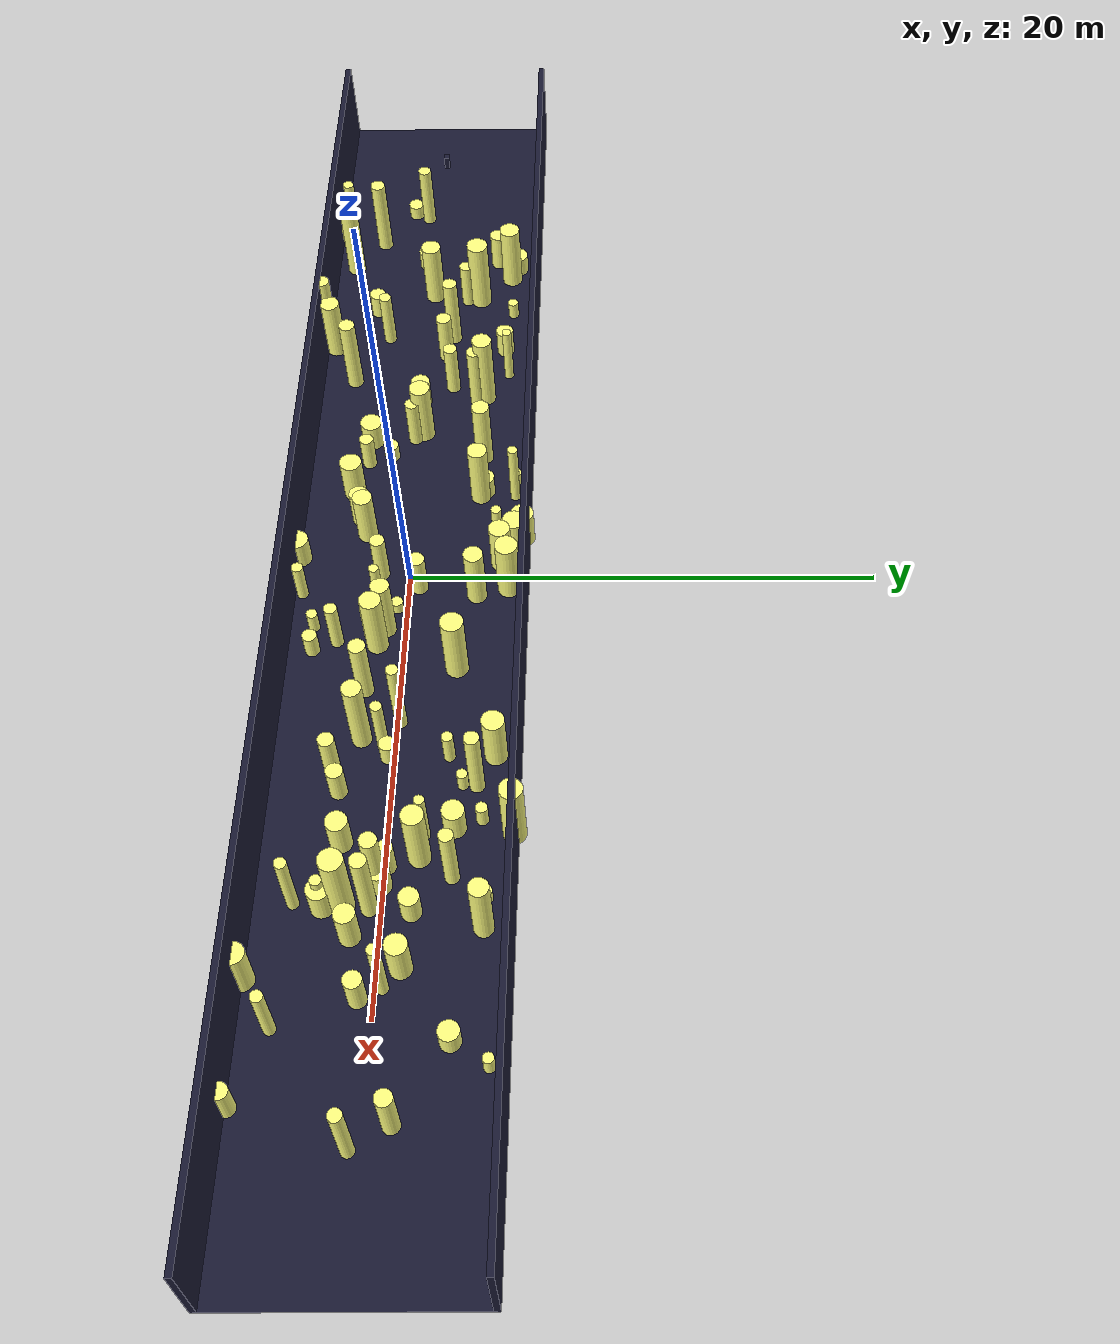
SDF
<?xml version="1.0"?>
<sdf version="1.4">
  <world name="default">
    <gui>
      <camera name="user_camera">
        <pose>-20 -30 40 0 0.66 0.83</pose>
      </camera>
    </gui>
    <include>
      <uri>model://ground_plane</uri>
    </include>
    <include>
      <uri>model://sun</uri>
    </include>
    <scene>
      <shadows>0</shadows>
    </scene>
    <model name="forest">
      <static>true</static>
      <link name="cylinder0">
        <pose>-3.192849726844482 3.5873826504181725 0.41820738886080283 0 0 0 </pose>
        <visual name="visual">
          <geometry>
            <cylinder>
              <radius>0.22529840313196697</radius>
              <length>0.8364147777216057</length>
            </cylinder>
          </geometry>
          <material>
            <ambient>0.6 0.6 0.6 1</ambient>
            <diffuse>1 1 0.5 1</diffuse>
            <specular>0 0 0</specular>
            <emissive>0 0 0 1</emissive>
          </material>
        </visual>
        <collision name="collision">
          <geometry>
            <cylinder>
              <radius>0.22529840313196697</radius>
              <length>0.8364147777216057</length>
            </cylinder>
          </geometry>
          <max_contacts>0</max_contacts>
        </collision>
      </link>
      <link name="cylinder1">
        <pose>-6.531154573892994 -2.2991554551917304 0.8637511969062655 0 0 0 </pose>
        <visual name="visual">
          <geometry>
            <cylinder>
              <radius>0.3069299705862069</radius>
              <length>1.727502393812531</length>
            </cylinder>
          </geometry>
          <material>
            <ambient>0.6 0.6 0.6 1</ambient>
            <diffuse>1 1 0.5 1</diffuse>
            <specular>0 0 0</specular>
            <emissive>0 0 0 1</emissive>
          </material>
        </visual>
        <collision name="collision">
          <geometry>
            <cylinder>
              <radius>0.3069299705862069</radius>
              <length>1.727502393812531</length>
            </cylinder>
          </geometry>
          <max_contacts>0</max_contacts>
        </collision>
      </link>
      <link name="cylinder2">
        <pose>12.17355871511667 2.617348784406312 0.7695251671588164 0 0 0 </pose>
        <visual name="visual">
          <geometry>
            <cylinder>
              <radius>0.45518470965374425</radius>
              <length>1.5390503343176327</length>
            </cylinder>
          </geometry>
          <material>
            <ambient>0.6 0.6 0.6 1</ambient>
            <diffuse>1 1 0.5 1</diffuse>
            <specular>0 0 0</specular>
            <emissive>0 0 0 1</emissive>
          </material>
        </visual>
        <collision name="collision">
          <geometry>
            <cylinder>
              <radius>0.45518470965374425</radius>
              <length>1.5390503343176327</length>
            </cylinder>
          </geometry>
          <max_contacts>0</max_contacts>
        </collision>
      </link>
      <link name="cylinder3">
        <pose>-7.840075381841473 -2.2307376366061327 0.6986270750220682 0 0 0 </pose>
        <visual name="visual">
          <geometry>
            <cylinder>
              <radius>0.48328531518326306</radius>
              <length>1.3972541500441364</length>
            </cylinder>
          </geometry>
          <material>
            <ambient>0.6 0.6 0.6 1</ambient>
            <diffuse>1 1 0.5 1</diffuse>
            <specular>0 0 0</specular>
            <emissive>0 0 0 1</emissive>
          </material>
        </visual>
        <collision name="collision">
          <geometry>
            <cylinder>
              <radius>0.48328531518326306</radius>
              <length>1.3972541500441364</length>
            </cylinder>
          </geometry>
          <max_contacts>0</max_contacts>
        </collision>
      </link>
      <link name="cylinder4">
        <pose>0.5451021397248006 4.287327093307088 1.5533532316845653 0 0 0 </pose>
        <visual name="visual">
          <geometry>
            <cylinder>
              <radius>0.490695693746299</radius>
              <length>3.1067064633691306</length>
            </cylinder>
          </geometry>
          <material>
            <ambient>0.6 0.6 0.6 1</ambient>
            <diffuse>1 1 0.5 1</diffuse>
            <specular>0 0 0</specular>
            <emissive>0 0 0 1</emissive>
          </material>
        </visual>
        <collision name="collision">
          <geometry>
            <cylinder>
              <radius>0.490695693746299</radius>
              <length>3.1067064633691306</length>
            </cylinder>
          </geometry>
          <max_contacts>0</max_contacts>
        </collision>
      </link>
      <link name="cylinder5">
        <pose>16.382690969800457 3.9296498198441725 1.7116452125746195 0 0 0 </pose>
        <visual name="visual">
          <geometry>
            <cylinder>
              <radius>0.40242538897291935</radius>
              <length>3.423290425149239</length>
            </cylinder>
          </geometry>
          <material>
            <ambient>0.6 0.6 0.6 1</ambient>
            <diffuse>1 1 0.5 1</diffuse>
            <specular>0 0 0</specular>
            <emissive>0 0 0 1</emissive>
          </material>
        </visual>
        <collision name="collision">
          <geometry>
            <cylinder>
              <radius>0.40242538897291935</radius>
              <length>3.423290425149239</length>
            </cylinder>
          </geometry>
          <max_contacts>0</max_contacts>
        </collision>
      </link>
      <link name="cylinder6">
        <pose>0.8219950260331892 -4.550754108827136 0.9829498164001 0 0 0 </pose>
        <visual name="visual">
          <geometry>
            <cylinder>
              <radius>0.2426356322146021</radius>
              <length>1.9658996328002</length>
            </cylinder>
          </geometry>
          <material>
            <ambient>0.6 0.6 0.6 1</ambient>
            <diffuse>1 1 0.5 1</diffuse>
            <specular>0 0 0</specular>
            <emissive>0 0 0 1</emissive>
          </material>
        </visual>
        <collision name="collision">
          <geometry>
            <cylinder>
              <radius>0.2426356322146021</radius>
              <length>1.9658996328002</length>
            </cylinder>
          </geometry>
          <max_contacts>0</max_contacts>
        </collision>
      </link>
      <link name="cylinder7">
        <pose>-10.284992835760514 -0.16313799900772352 0.731888011486953 0 0 0 </pose>
        <visual name="visual">
          <geometry>
            <cylinder>
              <radius>0.4293897891182539</radius>
              <length>1.463776022973906</length>
            </cylinder>
          </geometry>
          <material>
            <ambient>0.6 0.6 0.6 1</ambient>
            <diffuse>1 1 0.5 1</diffuse>
            <specular>0 0 0</specular>
            <emissive>0 0 0 1</emissive>
          </material>
        </visual>
        <collision name="collision">
          <geometry>
            <cylinder>
              <radius>0.4293897891182539</radius>
              <length>1.463776022973906</length>
            </cylinder>
          </geometry>
          <max_contacts>0</max_contacts>
        </collision>
      </link>
      <link name="cylinder8">
        <pose>14.62403911125039 -0.0837147885713696 0.6771761001458225 0 0 0 </pose>
        <visual name="visual">
          <geometry>
            <cylinder>
              <radius>0.4475435085670516</radius>
              <length>1.354352200291645</length>
            </cylinder>
          </geometry>
          <material>
            <ambient>0.6 0.6 0.6 1</ambient>
            <diffuse>1 1 0.5 1</diffuse>
            <specular>0 0 0</specular>
            <emissive>0 0 0 1</emissive>
          </material>
        </visual>
        <collision name="collision">
          <geometry>
            <cylinder>
              <radius>0.4475435085670516</radius>
              <length>1.354352200291645</length>
            </cylinder>
          </geometry>
          <max_contacts>0</max_contacts>
        </collision>
      </link>
      <link name="cylinder9">
        <pose>15.456999087174616 -1.4610693759416282 1.895710020783813 0 0 0 </pose>
        <visual name="visual">
          <geometry>
            <cylinder>
              <radius>0.48978377937480916</radius>
              <length>3.791420041567626</length>
            </cylinder>
          </geometry>
          <material>
            <ambient>0.6 0.6 0.6 1</ambient>
            <diffuse>1 1 0.5 1</diffuse>
            <specular>0 0 0</specular>
            <emissive>0 0 0 1</emissive>
          </material>
        </visual>
        <collision name="collision">
          <geometry>
            <cylinder>
              <radius>0.48978377937480916</radius>
              <length>3.791420041567626</length>
            </cylinder>
          </geometry>
          <max_contacts>0</max_contacts>
        </collision>
      </link>
      <link name="cylinder10">
        <pose>-0.22686120978561064 -1.2207896263014395 1.2268731282159098 0 0 0 </pose>
        <visual name="visual">
          <geometry>
            <cylinder>
              <radius>0.3159867367491881</radius>
              <length>2.4537462564318195</length>
            </cylinder>
          </geometry>
          <material>
            <ambient>0.6 0.6 0.6 1</ambient>
            <diffuse>1 1 0.5 1</diffuse>
            <specular>0 0 0</specular>
            <emissive>0 0 0 1</emissive>
          </material>
        </visual>
        <collision name="collision">
          <geometry>
            <cylinder>
              <radius>0.3159867367491881</radius>
              <length>2.4537462564318195</length>
            </cylinder>
          </geometry>
          <max_contacts>0</max_contacts>
        </collision>
      </link>
      <link name="cylinder11">
        <pose>8.878919479202033 4.079860358370427 1.3583442511263264 0 0 0 </pose>
        <visual name="visual">
          <geometry>
            <cylinder>
              <radius>0.4692062023084717</radius>
              <length>2.716688502252653</length>
            </cylinder>
          </geometry>
          <material>
            <ambient>0.6 0.6 0.6 1</ambient>
            <diffuse>1 1 0.5 1</diffuse>
            <specular>0 0 0</specular>
            <emissive>0 0 0 1</emissive>
          </material>
        </visual>
        <collision name="collision">
          <geometry>
            <cylinder>
              <radius>0.4692062023084717</radius>
              <length>2.716688502252653</length>
            </cylinder>
          </geometry>
          <max_contacts>0</max_contacts>
        </collision>
      </link>
      <link name="cylinder12">
        <pose>23.857496988495512 1.0411982424140138 1.3827535337328685 0 0 0 </pose>
        <visual name="visual">
          <geometry>
            <cylinder>
              <radius>0.3394898045034613</radius>
              <length>2.765507067465737</length>
            </cylinder>
          </geometry>
          <material>
            <ambient>0.6 0.6 0.6 1</ambient>
            <diffuse>1 1 0.5 1</diffuse>
            <specular>0 0 0</specular>
            <emissive>0 0 0 1</emissive>
          </material>
        </visual>
        <collision name="collision">
          <geometry>
            <cylinder>
              <radius>0.3394898045034613</radius>
              <length>2.765507067465737</length>
            </cylinder>
          </geometry>
          <max_contacts>0</max_contacts>
        </collision>
      </link>
      <link name="cylinder13">
        <pose>-1.6479260388239219 4.486018486528385 1.0291647151481158 0 0 0 </pose>
        <visual name="visual">
          <geometry>
            <cylinder>
              <radius>0.48310275463035407</radius>
              <length>2.0583294302962316</length>
            </cylinder>
          </geometry>
          <material>
            <ambient>0.6 0.6 0.6 1</ambient>
            <diffuse>1 1 0.5 1</diffuse>
            <specular>0 0 0</specular>
            <emissive>0 0 0 1</emissive>
          </material>
        </visual>
        <collision name="collision">
          <geometry>
            <cylinder>
              <radius>0.48310275463035407</radius>
              <length>2.0583294302962316</length>
            </cylinder>
          </geometry>
          <max_contacts>0</max_contacts>
        </collision>
      </link>
      <link name="cylinder14">
        <pose>-13.717309106918485 -4.482344821012548 1.5525525306366679 0 0 0 </pose>
        <visual name="visual">
          <geometry>
            <cylinder>
              <radius>0.4386502182769846</radius>
              <length>3.1051050612733357</length>
            </cylinder>
          </geometry>
          <material>
            <ambient>0.6 0.6 0.6 1</ambient>
            <diffuse>1 1 0.5 1</diffuse>
            <specular>0 0 0</specular>
            <emissive>0 0 0 1</emissive>
          </material>
        </visual>
        <collision name="collision">
          <geometry>
            <cylinder>
              <radius>0.4386502182769846</radius>
              <length>3.1051050612733357</length>
            </cylinder>
          </geometry>
          <max_contacts>0</max_contacts>
        </collision>
      </link>
      <link name="cylinder15">
        <pose>20.32863319259627 -3.6418209097069587 1.5089677672920634 0 0 0 </pose>
        <visual name="visual">
          <geometry>
            <cylinder>
              <radius>0.24420239186949372</radius>
              <length>3.0179355345841268</length>
            </cylinder>
          </geometry>
          <material>
            <ambient>0.6 0.6 0.6 1</ambient>
            <diffuse>1 1 0.5 1</diffuse>
            <specular>0 0 0</specular>
            <emissive>0 0 0 1</emissive>
          </material>
        </visual>
        <collision name="collision">
          <geometry>
            <cylinder>
              <radius>0.24420239186949372</radius>
              <length>3.0179355345841268</length>
            </cylinder>
          </geometry>
          <max_contacts>0</max_contacts>
        </collision>
      </link>
      <link name="cylinder16">
        <pose>-3.2949368990611134 -2.345796280695861 0.913958535475745 0 0 0 </pose>
        <visual name="visual">
          <geometry>
            <cylinder>
              <radius>0.42502396809160364</radius>
              <length>1.82791707095149</length>
            </cylinder>
          </geometry>
          <material>
            <ambient>0.6 0.6 0.6 1</ambient>
            <diffuse>1 1 0.5 1</diffuse>
            <specular>0 0 0</specular>
            <emissive>0 0 0 1</emissive>
          </material>
        </visual>
        <collision name="collision">
          <geometry>
            <cylinder>
              <radius>0.42502396809160364</radius>
              <length>1.82791707095149</length>
            </cylinder>
          </geometry>
          <max_contacts>0</max_contacts>
        </collision>
      </link>
      <link name="cylinder17">
        <pose>1.6294070108838419 -0.41041868526114555 0.3100170222696396 0 0 0 </pose>
        <visual name="visual">
          <geometry>
            <cylinder>
              <radius>0.25122345132233415</radius>
              <length>0.6200340445392792</length>
            </cylinder>
          </geometry>
          <material>
            <ambient>0.6 0.6 0.6 1</ambient>
            <diffuse>1 1 0.5 1</diffuse>
            <specular>0 0 0</specular>
            <emissive>0 0 0 1</emissive>
          </material>
        </visual>
        <collision name="collision">
          <geometry>
            <cylinder>
              <radius>0.25122345132233415</radius>
              <length>0.6200340445392792</length>
            </cylinder>
          </geometry>
          <max_contacts>0</max_contacts>
        </collision>
      </link>
      <link name="cylinder18">
        <pose>18.440453964464126 -4.842324224014992 1.208034778838587 0 0 0 </pose>
        <visual name="visual">
          <geometry>
            <cylinder>
              <radius>0.4564822820893654</radius>
              <length>2.416069557677174</length>
            </cylinder>
          </geometry>
          <material>
            <ambient>0.6 0.6 0.6 1</ambient>
            <diffuse>1 1 0.5 1</diffuse>
            <specular>0 0 0</specular>
            <emissive>0 0 0 1</emissive>
          </material>
        </visual>
        <collision name="collision">
          <geometry>
            <cylinder>
              <radius>0.4564822820893654</radius>
              <length>2.416069557677174</length>
            </cylinder>
          </geometry>
          <max_contacts>0</max_contacts>
        </collision>
      </link>
      <link name="cylinder19">
        <pose>-21.52139541314041 -4.799360331339456 0.3919770281490217 0 0 0 </pose>
        <visual name="visual">
          <geometry>
            <cylinder>
              <radius>0.3513322325659828</radius>
              <length>0.7839540562980434</length>
            </cylinder>
          </geometry>
          <material>
            <ambient>0.6 0.6 0.6 1</ambient>
            <diffuse>1 1 0.5 1</diffuse>
            <specular>0 0 0</specular>
            <emissive>0 0 0 1</emissive>
          </material>
        </visual>
        <collision name="collision">
          <geometry>
            <cylinder>
              <radius>0.3513322325659828</radius>
              <length>0.7839540562980434</length>
            </cylinder>
          </geometry>
          <max_contacts>0</max_contacts>
        </collision>
      </link>
      <link name="cylinder20">
        <pose>-16.022930730948598 3.8910977119118844 0.4477537448495911 0 0 0 </pose>
        <visual name="visual">
          <geometry>
            <cylinder>
              <radius>0.24179222421214583</radius>
              <length>0.8955074896991821</length>
            </cylinder>
          </geometry>
          <material>
            <ambient>0.6 0.6 0.6 1</ambient>
            <diffuse>1 1 0.5 1</diffuse>
            <specular>0 0 0</specular>
            <emissive>0 0 0 1</emissive>
          </material>
        </visual>
        <collision name="collision">
          <geometry>
            <cylinder>
              <radius>0.24179222421214583</radius>
              <length>0.8955074896991821</length>
            </cylinder>
          </geometry>
          <max_contacts>0</max_contacts>
        </collision>
      </link>
      <link name="cylinder21">
        <pose>-18.475527163501443 3.7433859103773717 1.661870806551407 0 0 0 </pose>
        <visual name="visual">
          <geometry>
            <cylinder>
              <radius>0.45883959178836686</radius>
              <length>3.323741613102814</length>
            </cylinder>
          </geometry>
          <material>
            <ambient>0.6 0.6 0.6 1</ambient>
            <diffuse>1 1 0.5 1</diffuse>
            <specular>0 0 0</specular>
            <emissive>0 0 0 1</emissive>
          </material>
        </visual>
        <collision name="collision">
          <geometry>
            <cylinder>
              <radius>0.45883959178836686</radius>
              <length>3.323741613102814</length>
            </cylinder>
          </geometry>
          <max_contacts>0</max_contacts>
        </collision>
      </link>
      <link name="cylinder22">
        <pose>-4.535254107145597 4.384111423506766 1.6392177718342351 0 0 0 </pose>
        <visual name="visual">
          <geometry>
            <cylinder>
              <radius>0.21562769942210844</radius>
              <length>3.2784355436684702</length>
            </cylinder>
          </geometry>
          <material>
            <ambient>0.6 0.6 0.6 1</ambient>
            <diffuse>1 1 0.5 1</diffuse>
            <specular>0 0 0</specular>
            <emissive>0 0 0 1</emissive>
          </material>
        </visual>
        <collision name="collision">
          <geometry>
            <cylinder>
              <radius>0.21562769942210844</radius>
              <length>3.2784355436684702</length>
            </cylinder>
          </geometry>
          <max_contacts>0</max_contacts>
        </collision>
      </link>
      <link name="cylinder23">
        <pose>18.78206764260443 0.32193979078497925 1.7154093065790716 0 0 0 </pose>
        <visual name="visual">
          <geometry>
            <cylinder>
              <radius>0.2384730306338957</radius>
              <length>3.4308186131581433</length>
            </cylinder>
          </geometry>
          <material>
            <ambient>0.6 0.6 0.6 1</ambient>
            <diffuse>1 1 0.5 1</diffuse>
            <specular>0 0 0</specular>
            <emissive>0 0 0 1</emissive>
          </material>
        </visual>
        <collision name="collision">
          <geometry>
            <cylinder>
              <radius>0.2384730306338957</radius>
              <length>3.4308186131581433</length>
            </cylinder>
          </geometry>
          <max_contacts>0</max_contacts>
        </collision>
      </link>
      <link name="cylinder24">
        <pose>-17.321003405382605 0.02377790525131296 1.6424565787959828 0 0 0 </pose>
        <visual name="visual">
          <geometry>
            <cylinder>
              <radius>0.4467246966665991</radius>
              <length>3.2849131575919657</length>
            </cylinder>
          </geometry>
          <material>
            <ambient>0.6 0.6 0.6 1</ambient>
            <diffuse>1 1 0.5 1</diffuse>
            <specular>0 0 0</specular>
            <emissive>0 0 0 1</emissive>
          </material>
        </visual>
        <collision name="collision">
          <geometry>
            <cylinder>
              <radius>0.4467246966665991</radius>
              <length>3.2849131575919657</length>
            </cylinder>
          </geometry>
          <max_contacts>0</max_contacts>
        </collision>
      </link>
      <link name="cylinder25">
        <pose>15.18038209791004 3.9632517767507522 0.3795768220333743 0 0 0 </pose>
        <visual name="visual">
          <geometry>
            <cylinder>
              <radius>0.2628267390274407</radius>
              <length>0.7591536440667486</length>
            </cylinder>
          </geometry>
          <material>
            <ambient>0.6 0.6 0.6 1</ambient>
            <diffuse>1 1 0.5 1</diffuse>
            <specular>0 0 0</specular>
            <emissive>0 0 0 1</emissive>
          </material>
        </visual>
        <collision name="collision">
          <geometry>
            <cylinder>
              <radius>0.2628267390274407</radius>
              <length>0.7591536440667486</length>
            </cylinder>
          </geometry>
          <max_contacts>0</max_contacts>
        </collision>
      </link>
      <link name="cylinder26">
        <pose>-14.343603194212061 -4.7722961267242265 1.9627895293435929 0 0 0 </pose>
        <visual name="visual">
          <geometry>
            <cylinder>
              <radius>0.31342925739843686</radius>
              <length>3.9255790586871857</length>
            </cylinder>
          </geometry>
          <material>
            <ambient>0.6 0.6 0.6 1</ambient>
            <diffuse>1 1 0.5 1</diffuse>
            <specular>0 0 0</specular>
            <emissive>0 0 0 1</emissive>
          </material>
        </visual>
        <collision name="collision">
          <geometry>
            <cylinder>
              <radius>0.31342925739843686</radius>
              <length>3.9255790586871857</length>
            </cylinder>
          </geometry>
          <max_contacts>0</max_contacts>
        </collision>
      </link>
      <link name="cylinder27">
        <pose>-11.185640867635904 1.2445072055534805 1.3479667729197307 0 0 0 </pose>
        <visual name="visual">
          <geometry>
            <cylinder>
              <radius>0.3088744043318439</radius>
              <length>2.6959335458394613</length>
            </cylinder>
          </geometry>
          <material>
            <ambient>0.6 0.6 0.6 1</ambient>
            <diffuse>1 1 0.5 1</diffuse>
            <specular>0 0 0</specular>
            <emissive>0 0 0 1</emissive>
          </material>
        </visual>
        <collision name="collision">
          <geometry>
            <cylinder>
              <radius>0.3088744043318439</radius>
              <length>2.6959335458394613</length>
            </cylinder>
          </geometry>
          <max_contacts>0</max_contacts>
        </collision>
      </link>
      <link name="cylinder28">
        <pose>-10.375347741907309 2.397718843863278 1.6562582636478846 0 0 0 </pose>
        <visual name="visual">
          <geometry>
            <cylinder>
              <radius>0.31791861940273086</radius>
              <length>3.3125165272957693</length>
            </cylinder>
          </geometry>
          <material>
            <ambient>0.6 0.6 0.6 1</ambient>
            <diffuse>1 1 0.5 1</diffuse>
            <specular>0 0 0</specular>
            <emissive>0 0 0 1</emissive>
          </material>
        </visual>
        <collision name="collision">
          <geometry>
            <cylinder>
              <radius>0.31791861940273086</radius>
              <length>3.3125165272957693</length>
            </cylinder>
          </geometry>
          <max_contacts>0</max_contacts>
        </collision>
      </link>
      <link name="cylinder29">
        <pose>-11.978202229633927 3.8230897167422953 1.4724057514765017 0 0 0 </pose>
        <visual name="visual">
          <geometry>
            <cylinder>
              <radius>0.20522275142655363</radius>
              <length>2.9448115029530033</length>
            </cylinder>
          </geometry>
          <material>
            <ambient>0.6 0.6 0.6 1</ambient>
            <diffuse>1 1 0.5 1</diffuse>
            <specular>0 0 0</specular>
            <emissive>0 0 0 1</emissive>
          </material>
        </visual>
        <collision name="collision">
          <geometry>
            <cylinder>
              <radius>0.20522275142655363</radius>
              <length>2.9448115029530033</length>
            </cylinder>
          </geometry>
          <max_contacts>0</max_contacts>
        </collision>
      </link>
      <link name="cylinder30">
        <pose>12.466454563471714 1.4634949548378549 1.4268033545715695 0 0 0 </pose>
        <visual name="visual">
          <geometry>
            <cylinder>
              <radius>0.20881695404905304</radius>
              <length>2.853606709143139</length>
            </cylinder>
          </geometry>
          <material>
            <ambient>0.6 0.6 0.6 1</ambient>
            <diffuse>1 1 0.5 1</diffuse>
            <specular>0 0 0</specular>
            <emissive>0 0 0 1</emissive>
          </material>
        </visual>
        <collision name="collision">
          <geometry>
            <cylinder>
              <radius>0.20881695404905304</radius>
              <length>2.853606709143139</length>
            </cylinder>
          </geometry>
          <max_contacts>0</max_contacts>
        </collision>
      </link>
      <link name="cylinder31">
        <pose>15.73953664509056 1.1715371120125715 0.7075776560475322 0 0 0 </pose>
        <visual name="visual">
          <geometry>
            <cylinder>
              <radius>0.4041041723390336</radius>
              <length>1.4151553120950644</length>
            </cylinder>
          </geometry>
          <material>
            <ambient>0.6 0.6 0.6 1</ambient>
            <diffuse>1 1 0.5 1</diffuse>
            <specular>0 0 0</specular>
            <emissive>0 0 0 1</emissive>
          </material>
        </visual>
        <collision name="collision">
          <geometry>
            <cylinder>
              <radius>0.4041041723390336</radius>
              <length>1.4151553120950644</length>
            </cylinder>
          </geometry>
          <max_contacts>0</max_contacts>
        </collision>
      </link>
      <link name="cylinder32">
        <pose>-22.933062753586945 -4.561366808859965 1.1676305453009026 0 0 0 </pose>
        <visual name="visual">
          <geometry>
            <cylinder>
              <radius>0.2557523275480341</radius>
              <length>2.335261090601805</length>
            </cylinder>
          </geometry>
          <material>
            <ambient>0.6 0.6 0.6 1</ambient>
            <diffuse>1 1 0.5 1</diffuse>
            <specular>0 0 0</specular>
            <emissive>0 0 0 1</emissive>
          </material>
        </visual>
        <collision name="collision">
          <geometry>
            <cylinder>
              <radius>0.2557523275480341</radius>
              <length>2.335261090601805</length>
            </cylinder>
          </geometry>
          <max_contacts>0</max_contacts>
        </collision>
      </link>
      <link name="cylinder33">
        <pose>19.200297235555233 -0.5566598012490411 0.9218042193405969 0 0 0 </pose>
        <visual name="visual">
          <geometry>
            <cylinder>
              <radius>0.3691931991757576</radius>
              <length>1.8436084386811937</length>
            </cylinder>
          </geometry>
          <material>
            <ambient>0.6 0.6 0.6 1</ambient>
            <diffuse>1 1 0.5 1</diffuse>
            <specular>0 0 0</specular>
            <emissive>0 0 0 1</emissive>
          </material>
        </visual>
        <collision name="collision">
          <geometry>
            <cylinder>
              <radius>0.3691931991757576</radius>
              <length>1.8436084386811937</length>
            </cylinder>
          </geometry>
          <max_contacts>0</max_contacts>
        </collision>
      </link>
      <link name="cylinder34">
        <pose>24.732433368093957 -0.4078893535844852 1.7801295612060917 0 0 0 </pose>
        <visual name="visual">
          <geometry>
            <cylinder>
              <radius>0.2683265457778024</radius>
              <length>3.5602591224121833</length>
            </cylinder>
          </geometry>
          <material>
            <ambient>0.6 0.6 0.6 1</ambient>
            <diffuse>1 1 0.5 1</diffuse>
            <specular>0 0 0</specular>
            <emissive>0 0 0 1</emissive>
          </material>
        </visual>
        <collision name="collision">
          <geometry>
            <cylinder>
              <radius>0.2683265457778024</radius>
              <length>3.5602591224121833</length>
            </cylinder>
          </geometry>
          <max_contacts>0</max_contacts>
        </collision>
      </link>
      <link name="cylinder35">
        <pose>2.2000767860501824 -1.0098003690205126 1.8597760949323536 0 0 0 </pose>
        <visual name="visual">
          <geometry>
            <cylinder>
              <radius>0.20629073970940587</radius>
              <length>3.7195521898647073</length>
            </cylinder>
          </geometry>
          <material>
            <ambient>0.6 0.6 0.6 1</ambient>
            <diffuse>1 1 0.5 1</diffuse>
            <specular>0 0 0</specular>
            <emissive>0 0 0 1</emissive>
          </material>
        </visual>
        <collision name="collision">
          <geometry>
            <cylinder>
              <radius>0.20629073970940587</radius>
              <length>3.7195521898647073</length>
            </cylinder>
          </geometry>
          <max_contacts>0</max_contacts>
        </collision>
      </link>
      <link name="cylinder36">
        <pose>-6.927439370681405 -1.300475320676795 0.43946229399103265 0 0 0 </pose>
        <visual name="visual">
          <geometry>
            <cylinder>
              <radius>0.3275929531164651</radius>
              <length>0.8789245879820653</length>
            </cylinder>
          </geometry>
          <material>
            <ambient>0.6 0.6 0.6 1</ambient>
            <diffuse>1 1 0.5 1</diffuse>
            <specular>0 0 0</specular>
            <emissive>0 0 0 1</emissive>
          </material>
        </visual>
        <collision name="collision">
          <geometry>
            <cylinder>
              <radius>0.3275929531164651</radius>
              <length>0.8789245879820653</length>
            </cylinder>
          </geometry>
          <max_contacts>0</max_contacts>
        </collision>
      </link>
      <link name="cylinder37">
        <pose>3.3268651791632635 -2.832557597410086 1.2444173037912731 0 0 0 </pose>
        <visual name="visual">
          <geometry>
            <cylinder>
              <radius>0.27344529421121677</radius>
              <length>2.4888346075825463</length>
            </cylinder>
          </geometry>
          <material>
            <ambient>0.6 0.6 0.6 1</ambient>
            <diffuse>1 1 0.5 1</diffuse>
            <specular>0 0 0</specular>
            <emissive>0 0 0 1</emissive>
          </material>
        </visual>
        <collision name="collision">
          <geometry>
            <cylinder>
              <radius>0.27344529421121677</radius>
              <length>2.4888346075825463</length>
            </cylinder>
          </geometry>
          <max_contacts>0</max_contacts>
        </collision>
      </link>
      <link name="cylinder38">
        <pose>8.944952612057648 2.2216570837131364 0.8179286366309981 0 0 0 </pose>
        <visual name="visual">
          <geometry>
            <cylinder>
              <radius>0.23313235281679032</radius>
              <length>1.6358572732619963</length>
            </cylinder>
          </geometry>
          <material>
            <ambient>0.6 0.6 0.6 1</ambient>
            <diffuse>1 1 0.5 1</diffuse>
            <specular>0 0 0</specular>
            <emissive>0 0 0 1</emissive>
          </material>
        </visual>
        <collision name="collision">
          <geometry>
            <cylinder>
              <radius>0.23313235281679032</radius>
              <length>1.6358572732619963</length>
            </cylinder>
          </geometry>
          <max_contacts>0</max_contacts>
        </collision>
      </link>
      <link name="cylinder39">
        <pose>15.506929338213197 -2.2096749711047825 0.7948044124810728 0 0 0 </pose>
        <visual name="visual">
          <geometry>
            <cylinder>
              <radius>0.4772542039277148</radius>
              <length>1.5896088249621456</length>
            </cylinder>
          </geometry>
          <material>
            <ambient>0.6 0.6 0.6 1</ambient>
            <diffuse>1 1 0.5 1</diffuse>
            <specular>0 0 0</specular>
            <emissive>0 0 0 1</emissive>
          </material>
        </visual>
        <collision name="collision">
          <geometry>
            <cylinder>
              <radius>0.4772542039277148</radius>
              <length>1.5896088249621456</length>
            </cylinder>
          </geometry>
          <max_contacts>0</max_contacts>
        </collision>
      </link>
      <link name="cylinder40">
        <pose>-19.617193351092453 3.0552382854576514 0.9829191595916573 0 0 0 </pose>
        <visual name="visual">
          <geometry>
            <cylinder>
              <radius>0.36671551089279053</radius>
              <length>1.9658383191833146</length>
            </cylinder>
          </geometry>
          <material>
            <ambient>0.6 0.6 0.6 1</ambient>
            <diffuse>1 1 0.5 1</diffuse>
            <specular>0 0 0</specular>
            <emissive>0 0 0 1</emissive>
          </material>
        </visual>
        <collision name="collision">
          <geometry>
            <cylinder>
              <radius>0.36671551089279053</radius>
              <length>1.9658383191833146</length>
            </cylinder>
          </geometry>
          <max_contacts>0</max_contacts>
        </collision>
      </link>
      <link name="cylinder41">
        <pose>14.489343630699338 -0.21784645105941003 1.731855769582506 0 0 0 </pose>
        <visual name="visual">
          <geometry>
            <cylinder>
              <radius>0.3526989026732716</radius>
              <length>3.463711539165012</length>
            </cylinder>
          </geometry>
          <material>
            <ambient>0.6 0.6 0.6 1</ambient>
            <diffuse>1 1 0.5 1</diffuse>
            <specular>0 0 0</specular>
            <emissive>0 0 0 1</emissive>
          </material>
        </visual>
        <collision name="collision">
          <geometry>
            <cylinder>
              <radius>0.3526989026732716</radius>
              <length>3.463711539165012</length>
            </cylinder>
          </geometry>
          <max_contacts>0</max_contacts>
        </collision>
      </link>
      <link name="cylinder42">
        <pose>15.596232416822524 -0.42684086194105664 1.9987643856446065 0 0 0 </pose>
        <visual name="visual">
          <geometry>
            <cylinder>
              <radius>0.33143724376177514</radius>
              <length>3.997528771289213</length>
            </cylinder>
          </geometry>
          <material>
            <ambient>0.6 0.6 0.6 1</ambient>
            <diffuse>1 1 0.5 1</diffuse>
            <specular>0 0 0</specular>
            <emissive>0 0 0 1</emissive>
          </material>
        </visual>
        <collision name="collision">
          <geometry>
            <cylinder>
              <radius>0.33143724376177514</radius>
              <length>3.997528771289213</length>
            </cylinder>
          </geometry>
          <max_contacts>0</max_contacts>
        </collision>
      </link>
      <link name="cylinder43">
        <pose>-0.7968589158950721 3.915933726437169 1.2687810697210444 0 0 0 </pose>
        <visual name="visual">
          <geometry>
            <cylinder>
              <radius>0.4544519215467621</radius>
              <length>2.537562139442089</length>
            </cylinder>
          </geometry>
          <material>
            <ambient>0.6 0.6 0.6 1</ambient>
            <diffuse>1 1 0.5 1</diffuse>
            <specular>0 0 0</specular>
            <emissive>0 0 0 1</emissive>
          </material>
        </visual>
        <collision name="collision">
          <geometry>
            <cylinder>
              <radius>0.4544519215467621</radius>
              <length>2.537562139442089</length>
            </cylinder>
          </geometry>
          <max_contacts>0</max_contacts>
        </collision>
      </link>
      <link name="cylinder44">
        <pose>-16.966308467028362 1.6498239983056706 1.1904611856741492 0 0 0 </pose>
        <visual name="visual">
          <geometry>
            <cylinder>
              <radius>0.29661769156286455</radius>
              <length>2.3809223713482983</length>
            </cylinder>
          </geometry>
          <material>
            <ambient>0.6 0.6 0.6 1</ambient>
            <diffuse>1 1 0.5 1</diffuse>
            <specular>0 0 0</specular>
            <emissive>0 0 0 1</emissive>
          </material>
        </visual>
        <collision name="collision">
          <geometry>
            <cylinder>
              <radius>0.29661769156286455</radius>
              <length>2.3809223713482983</length>
            </cylinder>
          </geometry>
          <max_contacts>0</max_contacts>
        </collision>
      </link>
      <link name="cylinder45">
        <pose>-23.242238410512115 -1.298396019229414 0.3860815771462779 0 0 0 </pose>
        <visual name="visual">
          <geometry>
            <cylinder>
              <radius>0.3566798289988673</radius>
              <length>0.7721631542925558</length>
            </cylinder>
          </geometry>
          <material>
            <ambient>0.6 0.6 0.6 1</ambient>
            <diffuse>1 1 0.5 1</diffuse>
            <specular>0 0 0</specular>
            <emissive>0 0 0 1</emissive>
          </material>
        </visual>
        <collision name="collision">
          <geometry>
            <cylinder>
              <radius>0.3566798289988673</radius>
              <length>0.7721631542925558</length>
            </cylinder>
          </geometry>
          <max_contacts>0</max_contacts>
        </collision>
      </link>
      <link name="cylinder46">
        <pose>13.439167088054063 1.3241548024242134 1.7184270815577272 0 0 0 </pose>
        <visual name="visual">
          <geometry>
            <cylinder>
              <radius>0.4499449676625704</radius>
              <length>3.4368541631154543</length>
            </cylinder>
          </geometry>
          <material>
            <ambient>0.6 0.6 0.6 1</ambient>
            <diffuse>1 1 0.5 1</diffuse>
            <specular>0 0 0</specular>
            <emissive>0 0 0 1</emissive>
          </material>
        </visual>
        <collision name="collision">
          <geometry>
            <cylinder>
              <radius>0.4499449676625704</radius>
              <length>3.4368541631154543</length>
            </cylinder>
          </geometry>
          <max_contacts>0</max_contacts>
        </collision>
      </link>
      <link name="cylinder47">
        <pose>-8.315415345329512 0.07293625856197927 1.5698973765842383 0 0 0 </pose>
        <visual name="visual">
          <geometry>
            <cylinder>
              <radius>0.4568266699394549</radius>
              <length>3.1397947531684767</length>
            </cylinder>
          </geometry>
          <material>
            <ambient>0.6 0.6 0.6 1</ambient>
            <diffuse>1 1 0.5 1</diffuse>
            <specular>0 0 0</specular>
            <emissive>0 0 0 1</emissive>
          </material>
        </visual>
        <collision name="collision">
          <geometry>
            <cylinder>
              <radius>0.4568266699394549</radius>
              <length>3.1397947531684767</length>
            </cylinder>
          </geometry>
          <max_contacts>0</max_contacts>
        </collision>
      </link>
      <link name="cylinder48">
        <pose>-19.14534681637143 3.6872108470854528 1.05835725443846 0 0 0 </pose>
        <visual name="visual">
          <geometry>
            <cylinder>
              <radius>0.23886587185151642</radius>
              <length>2.11671450887692</length>
            </cylinder>
          </geometry>
          <material>
            <ambient>0.6 0.6 0.6 1</ambient>
            <diffuse>1 1 0.5 1</diffuse>
            <specular>0 0 0</specular>
            <emissive>0 0 0 1</emissive>
          </material>
        </visual>
        <collision name="collision">
          <geometry>
            <cylinder>
              <radius>0.23886587185151642</radius>
              <length>2.11671450887692</length>
            </cylinder>
          </geometry>
          <max_contacts>0</max_contacts>
        </collision>
      </link>
      <link name="cylinder49">
        <pose>20.81168345473008 2.928617343516886 0.54699325148576 0 0 0 </pose>
        <visual name="visual">
          <geometry>
            <cylinder>
              <radius>0.41962012148468575</radius>
              <length>1.09398650297152</length>
            </cylinder>
          </geometry>
          <material>
            <ambient>0.6 0.6 0.6 1</ambient>
            <diffuse>1 1 0.5 1</diffuse>
            <specular>0 0 0</specular>
            <emissive>0 0 0 1</emissive>
          </material>
        </visual>
        <collision name="collision">
          <geometry>
            <cylinder>
              <radius>0.41962012148468575</radius>
              <length>1.09398650297152</length>
            </cylinder>
          </geometry>
          <max_contacts>0</max_contacts>
        </collision>
      </link>
      <link name="cylinder50">
        <pose>13.836993050028077 0.13474181616119552 0.8172512902104683 0 0 0 </pose>
        <visual name="visual">
          <geometry>
            <cylinder>
              <radius>0.330910202041312</radius>
              <length>1.6345025804209365</length>
            </cylinder>
          </geometry>
          <material>
            <ambient>0.6 0.6 0.6 1</ambient>
            <diffuse>1 1 0.5 1</diffuse>
            <specular>0 0 0</specular>
            <emissive>0 0 0 1</emissive>
          </material>
        </visual>
        <collision name="collision">
          <geometry>
            <cylinder>
              <radius>0.330910202041312</radius>
              <length>1.6345025804209365</length>
            </cylinder>
          </geometry>
          <max_contacts>0</max_contacts>
        </collision>
      </link>
      <link name="cylinder51">
        <pose>-13.24604810025954 0.818495764659243 1.293570343791727 0 0 0 </pose>
        <visual name="visual">
          <geometry>
            <cylinder>
              <radius>0.34008352765678296</radius>
              <length>2.587140687583454</length>
            </cylinder>
          </geometry>
          <material>
            <ambient>0.6 0.6 0.6 1</ambient>
            <diffuse>1 1 0.5 1</diffuse>
            <specular>0 0 0</specular>
            <emissive>0 0 0 1</emissive>
          </material>
        </visual>
        <collision name="collision">
          <geometry>
            <cylinder>
              <radius>0.34008352765678296</radius>
              <length>2.587140687583454</length>
            </cylinder>
          </geometry>
          <max_contacts>0</max_contacts>
        </collision>
      </link>
      <link name="cylinder52">
        <pose>2.7045159463375086 -0.787005885120589 1.6008697981100701 0 0 0 </pose>
        <visual name="visual">
          <geometry>
            <cylinder>
              <radius>0.39509654069503153</radius>
              <length>3.2017395962201403</length>
            </cylinder>
          </geometry>
          <material>
            <ambient>0.6 0.6 0.6 1</ambient>
            <diffuse>1 1 0.5 1</diffuse>
            <specular>0 0 0</specular>
            <emissive>0 0 0 1</emissive>
          </material>
        </visual>
        <collision name="collision">
          <geometry>
            <cylinder>
              <radius>0.39509654069503153</radius>
              <length>3.2017395962201403</length>
            </cylinder>
          </geometry>
          <max_contacts>0</max_contacts>
        </collision>
      </link>
      <link name="cylinder53">
        <pose>0.927405932077459 2.926455855577661 1.492132570759678 0 0 0 </pose>
        <visual name="visual">
          <geometry>
            <cylinder>
              <radius>0.4193248782191068</radius>
              <length>2.984265141519356</length>
            </cylinder>
          </geometry>
          <material>
            <ambient>0.6 0.6 0.6 1</ambient>
            <diffuse>1 1 0.5 1</diffuse>
            <specular>0 0 0</specular>
            <emissive>0 0 0 1</emissive>
          </material>
        </visual>
        <collision name="collision">
          <geometry>
            <cylinder>
              <radius>0.4193248782191068</radius>
              <length>2.984265141519356</length>
            </cylinder>
          </geometry>
          <max_contacts>0</max_contacts>
        </collision>
      </link>
      <link name="cylinder54">
        <pose>-4.645652061191736 4.4955602661596075 0.8244760821237908 0 0 0 </pose>
        <visual name="visual">
          <geometry>
            <cylinder>
              <radius>0.21961359601710717</radius>
              <length>1.6489521642475815</length>
            </cylinder>
          </geometry>
          <material>
            <ambient>0.6 0.6 0.6 1</ambient>
            <diffuse>1 1 0.5 1</diffuse>
            <specular>0 0 0</specular>
            <emissive>0 0 0 1</emissive>
          </material>
        </visual>
        <collision name="collision">
          <geometry>
            <cylinder>
              <radius>0.21961359601710717</radius>
              <length>1.6489521642475815</length>
            </cylinder>
          </geometry>
          <max_contacts>0</max_contacts>
        </collision>
      </link>
      <link name="cylinder55">
        <pose>12.804423549938008 -1.7562708476605726 0.921033869204892 0 0 0 </pose>
        <visual name="visual">
          <geometry>
            <cylinder>
              <radius>0.4482198343066287</radius>
              <length>1.842067738409784</length>
            </cylinder>
          </geometry>
          <material>
            <ambient>0.6 0.6 0.6 1</ambient>
            <diffuse>1 1 0.5 1</diffuse>
            <specular>0 0 0</specular>
            <emissive>0 0 0 1</emissive>
          </material>
        </visual>
        <collision name="collision">
          <geometry>
            <cylinder>
              <radius>0.4482198343066287</radius>
              <length>1.842067738409784</length>
            </cylinder>
          </geometry>
          <max_contacts>0</max_contacts>
        </collision>
      </link>
      <link name="cylinder56">
        <pose>-2.4037501720572934 -2.020563672012404 1.3325415203637436 0 0 0 </pose>
        <visual name="visual">
          <geometry>
            <cylinder>
              <radius>0.4285643957914931</radius>
              <length>2.6650830407274873</length>
            </cylinder>
          </geometry>
          <material>
            <ambient>0.6 0.6 0.6 1</ambient>
            <diffuse>1 1 0.5 1</diffuse>
            <specular>0 0 0</specular>
            <emissive>0 0 0 1</emissive>
          </material>
        </visual>
        <collision name="collision">
          <geometry>
            <cylinder>
              <radius>0.4285643957914931</radius>
              <length>2.6650830407274873</length>
            </cylinder>
          </geometry>
          <max_contacts>0</max_contacts>
        </collision>
      </link>
      <link name="cylinder57">
        <pose>3.4896654946446297 -1.115549225749625 1.6420080818517513 0 0 0 </pose>
        <visual name="visual">
          <geometry>
            <cylinder>
              <radius>0.4537127796081549</radius>
              <length>3.2840161637035026</length>
            </cylinder>
          </geometry>
          <material>
            <ambient>0.6 0.6 0.6 1</ambient>
            <diffuse>1 1 0.5 1</diffuse>
            <specular>0 0 0</specular>
            <emissive>0 0 0 1</emissive>
          </material>
        </visual>
        <collision name="collision">
          <geometry>
            <cylinder>
              <radius>0.4537127796081549</radius>
              <length>3.2840161637035026</length>
            </cylinder>
          </geometry>
          <max_contacts>0</max_contacts>
        </collision>
      </link>
      <link name="cylinder58">
        <pose>-16.223436627568937 -2.6358226408781738 0.639615828912053 0 0 0 </pose>
        <visual name="visual">
          <geometry>
            <cylinder>
              <radius>0.3692438282645588</radius>
              <length>1.279231657824106</length>
            </cylinder>
          </geometry>
          <material>
            <ambient>0.6 0.6 0.6 1</ambient>
            <diffuse>1 1 0.5 1</diffuse>
            <specular>0 0 0</specular>
            <emissive>0 0 0 1</emissive>
          </material>
        </visual>
        <collision name="collision">
          <geometry>
            <cylinder>
              <radius>0.3692438282645588</radius>
              <length>1.279231657824106</length>
            </cylinder>
          </geometry>
          <max_contacts>0</max_contacts>
        </collision>
      </link>
      <link name="cylinder59">
        <pose>-4.833804361718109 3.011883279083353 0.558730807152031 0 0 0 </pose>
        <visual name="visual">
          <geometry>
            <cylinder>
              <radius>0.44148800575297126</radius>
              <length>1.117461614304062</length>
            </cylinder>
          </geometry>
          <material>
            <ambient>0.6 0.6 0.6 1</ambient>
            <diffuse>1 1 0.5 1</diffuse>
            <specular>0 0 0</specular>
            <emissive>0 0 0 1</emissive>
          </material>
        </visual>
        <collision name="collision">
          <geometry>
            <cylinder>
              <radius>0.44148800575297126</radius>
              <length>1.117461614304062</length>
            </cylinder>
          </geometry>
          <max_contacts>0</max_contacts>
        </collision>
      </link>
      <link name="cylinder60">
        <pose>10.276058038939958 3.386741249278746 1.8502091323024195 0 0 0 </pose>
        <visual name="visual">
          <geometry>
            <cylinder>
              <radius>0.308947790154439</radius>
              <length>3.700418264604839</length>
            </cylinder>
          </geometry>
          <material>
            <ambient>0.6 0.6 0.6 1</ambient>
            <diffuse>1 1 0.5 1</diffuse>
            <specular>0 0 0</specular>
            <emissive>0 0 0 1</emissive>
          </material>
        </visual>
        <collision name="collision">
          <geometry>
            <cylinder>
              <radius>0.308947790154439</radius>
              <length>3.700418264604839</length>
            </cylinder>
          </geometry>
          <max_contacts>0</max_contacts>
        </collision>
      </link>
      <link name="cylinder61">
        <pose>-10.542345697944755 2.796629027205281 1.932119978304161 0 0 0 </pose>
        <visual name="visual">
          <geometry>
            <cylinder>
              <radius>0.4419601165467153</radius>
              <length>3.864239956608322</length>
            </cylinder>
          </geometry>
          <material>
            <ambient>0.6 0.6 0.6 1</ambient>
            <diffuse>1 1 0.5 1</diffuse>
            <specular>0 0 0</specular>
            <emissive>0 0 0 1</emissive>
          </material>
        </visual>
        <collision name="collision">
          <geometry>
            <cylinder>
              <radius>0.4419601165467153</radius>
              <length>3.864239956608322</length>
            </cylinder>
          </geometry>
          <max_contacts>0</max_contacts>
        </collision>
      </link>
      <link name="cylinder62">
        <pose>7.3290191008465655 0.15591134739980284 1.9796183557118858 0 0 0 </pose>
        <visual name="visual">
          <geometry>
            <cylinder>
              <radius>0.2520362077839969</radius>
              <length>3.9592367114237716</length>
            </cylinder>
          </geometry>
          <material>
            <ambient>0.6 0.6 0.6 1</ambient>
            <diffuse>1 1 0.5 1</diffuse>
            <specular>0 0 0</specular>
            <emissive>0 0 0 1</emissive>
          </material>
        </visual>
        <collision name="collision">
          <geometry>
            <cylinder>
              <radius>0.2520362077839969</radius>
              <length>3.9592367114237716</length>
            </cylinder>
          </geometry>
          <max_contacts>0</max_contacts>
        </collision>
      </link>
      <link name="cylinder63">
        <pose>11.805849253504604 3.6740827512813663 0.5412694871013315 0 0 0 </pose>
        <visual name="visual">
          <geometry>
            <cylinder>
              <radius>0.24532652148197925</radius>
              <length>1.082538974202663</length>
            </cylinder>
          </geometry>
          <material>
            <ambient>0.6 0.6 0.6 1</ambient>
            <diffuse>1 1 0.5 1</diffuse>
            <specular>0 0 0</specular>
            <emissive>0 0 0 1</emissive>
          </material>
        </visual>
        <collision name="collision">
          <geometry>
            <cylinder>
              <radius>0.24532652148197925</radius>
              <length>1.082538974202663</length>
            </cylinder>
          </geometry>
          <max_contacts>0</max_contacts>
        </collision>
      </link>
      <link name="cylinder64">
        <pose>15.33967509791475 -2.2590286480247466 0.9836531245159008 0 0 0 </pose>
        <visual name="visual">
          <geometry>
            <cylinder>
              <radius>0.2349544484722807</radius>
              <length>1.9673062490318016</length>
            </cylinder>
          </geometry>
          <material>
            <ambient>0.6 0.6 0.6 1</ambient>
            <diffuse>1 1 0.5 1</diffuse>
            <specular>0 0 0</specular>
            <emissive>0 0 0 1</emissive>
          </material>
        </visual>
        <collision name="collision">
          <geometry>
            <cylinder>
              <radius>0.2349544484722807</radius>
              <length>1.9673062490318016</length>
            </cylinder>
          </geometry>
          <max_contacts>0</max_contacts>
        </collision>
      </link>
      <link name="cylinder65">
        <pose>-17.003328164011222 2.271189466586483 1.844629039812176 0 0 0 </pose>
        <visual name="visual">
          <geometry>
            <cylinder>
              <radius>0.4836389146505552</radius>
              <length>3.689258079624352</length>
            </cylinder>
          </geometry>
          <material>
            <ambient>0.6 0.6 0.6 1</ambient>
            <diffuse>1 1 0.5 1</diffuse>
            <specular>0 0 0</specular>
            <emissive>0 0 0 1</emissive>
          </material>
        </visual>
        <collision name="collision">
          <geometry>
            <cylinder>
              <radius>0.4836389146505552</radius>
              <length>3.689258079624352</length>
            </cylinder>
          </geometry>
          <max_contacts>0</max_contacts>
        </collision>
      </link>
      <link name="cylinder66">
        <pose>-14.418765345843687 1.1102216565047325 1.838638379085933 0 0 0 </pose>
        <visual name="visual">
          <geometry>
            <cylinder>
              <radius>0.32853140967150973</radius>
              <length>3.677276758171866</length>
            </cylinder>
          </geometry>
          <material>
            <ambient>0.6 0.6 0.6 1</ambient>
            <diffuse>1 1 0.5 1</diffuse>
            <specular>0 0 0</specular>
            <emissive>0 0 0 1</emissive>
          </material>
        </visual>
        <collision name="collision">
          <geometry>
            <cylinder>
              <radius>0.32853140967150973</radius>
              <length>3.677276758171866</length>
            </cylinder>
          </geometry>
          <max_contacts>0</max_contacts>
        </collision>
      </link>
      <link name="cylinder67">
        <pose>12.374200654205367 4.950567793063341 1.7494851448672644 0 0 0 </pose>
        <visual name="visual">
          <geometry>
            <cylinder>
              <radius>0.4720444157505522</radius>
              <length>3.4989702897345287</length>
            </cylinder>
          </geometry>
          <material>
            <ambient>0.6 0.6 0.6 1</ambient>
            <diffuse>1 1 0.5 1</diffuse>
            <specular>0 0 0</specular>
            <emissive>0 0 0 1</emissive>
          </material>
        </visual>
        <collision name="collision">
          <geometry>
            <cylinder>
              <radius>0.4720444157505522</radius>
              <length>3.4989702897345287</length>
            </cylinder>
          </geometry>
          <max_contacts>0</max_contacts>
        </collision>
      </link>
      <link name="cylinder68">
        <pose>0.5154638344089584 0.44510947290544145 1.061932650878334 0 0 0 </pose>
        <visual name="visual">
          <geometry>
            <cylinder>
              <radius>0.3559748003883073</radius>
              <length>2.123865301756668</length>
            </cylinder>
          </geometry>
          <material>
            <ambient>0.6 0.6 0.6 1</ambient>
            <diffuse>1 1 0.5 1</diffuse>
            <specular>0 0 0</specular>
            <emissive>0 0 0 1</emissive>
          </material>
        </visual>
        <collision name="collision">
          <geometry>
            <cylinder>
              <radius>0.3559748003883073</radius>
              <length>2.123865301756668</length>
            </cylinder>
          </geometry>
          <max_contacts>0</max_contacts>
        </collision>
      </link>
      <link name="cylinder69">
        <pose>-2.2240508841962594 4.81060729003705 0.8901127470546064 0 0 0 </pose>
        <visual name="visual">
          <geometry>
            <cylinder>
              <radius>0.4976981120629211</radius>
              <length>1.7802254941092128</length>
            </cylinder>
          </geometry>
          <material>
            <ambient>0.6 0.6 0.6 1</ambient>
            <diffuse>1 1 0.5 1</diffuse>
            <specular>0 0 0</specular>
            <emissive>0 0 0 1</emissive>
          </material>
        </visual>
        <collision name="collision">
          <geometry>
            <cylinder>
              <radius>0.4976981120629211</radius>
              <length>1.7802254941092128</length>
            </cylinder>
          </geometry>
          <max_contacts>0</max_contacts>
        </collision>
      </link>
      <link name="cylinder70">
        <pose>14.285695051369999 2.6257159518421354 1.7179923736178238 0 0 0 </pose>
        <visual name="visual">
          <geometry>
            <cylinder>
              <radius>0.2931016993940348</radius>
              <length>3.4359847472356475</length>
            </cylinder>
          </geometry>
          <material>
            <ambient>0.6 0.6 0.6 1</ambient>
            <diffuse>1 1 0.5 1</diffuse>
            <specular>0 0 0</specular>
            <emissive>0 0 0 1</emissive>
          </material>
        </visual>
        <collision name="collision">
          <geometry>
            <cylinder>
              <radius>0.2931016993940348</radius>
              <length>3.4359847472356475</length>
            </cylinder>
          </geometry>
          <max_contacts>0</max_contacts>
        </collision>
      </link>
      <link name="cylinder71">
        <pose>8.102474956606308 -1.3725759264189632 1.914699165471288 0 0 0 </pose>
        <visual name="visual">
          <geometry>
            <cylinder>
              <radius>0.40486415962533734</radius>
              <length>3.829398330942576</length>
            </cylinder>
          </geometry>
          <material>
            <ambient>0.6 0.6 0.6 1</ambient>
            <diffuse>1 1 0.5 1</diffuse>
            <specular>0 0 0</specular>
            <emissive>0 0 0 1</emissive>
          </material>
        </visual>
        <collision name="collision">
          <geometry>
            <cylinder>
              <radius>0.40486415962533734</radius>
              <length>3.829398330942576</length>
            </cylinder>
          </geometry>
          <max_contacts>0</max_contacts>
        </collision>
      </link>
      <link name="cylinder72">
        <pose>-20.99148614963648 -2.737000166826941 1.9746754435319942 0 0 0 </pose>
        <visual name="visual">
          <geometry>
            <cylinder>
              <radius>0.33717344354309686</radius>
              <length>3.9493508870639884</length>
            </cylinder>
          </geometry>
          <material>
            <ambient>0.6 0.6 0.6 1</ambient>
            <diffuse>1 1 0.5 1</diffuse>
            <specular>0 0 0</specular>
            <emissive>0 0 0 1</emissive>
          </material>
        </visual>
        <collision name="collision">
          <geometry>
            <cylinder>
              <radius>0.33717344354309686</radius>
              <length>3.9493508870639884</length>
            </cylinder>
          </geometry>
          <max_contacts>0</max_contacts>
        </collision>
      </link>
      <link name="cylinder73">
        <pose>17.996794814463108 0.9357022721209054 1.0757930091415022 0 0 0 </pose>
        <visual name="visual">
          <geometry>
            <cylinder>
              <radius>0.450443257757482</radius>
              <length>2.1515860182830044</length>
            </cylinder>
          </geometry>
          <material>
            <ambient>0.6 0.6 0.6 1</ambient>
            <diffuse>1 1 0.5 1</diffuse>
            <specular>0 0 0</specular>
            <emissive>0 0 0 1</emissive>
          </material>
        </visual>
        <collision name="collision">
          <geometry>
            <cylinder>
              <radius>0.450443257757482</radius>
              <length>2.1515860182830044</length>
            </cylinder>
          </geometry>
          <max_contacts>0</max_contacts>
        </collision>
      </link>
      <link name="cylinder74">
        <pose>8.421307360547345 -0.4742759358230506 1.5261590711259467 0 0 0 </pose>
        <visual name="visual">
          <geometry>
            <cylinder>
              <radius>0.23880693193115116</radius>
              <length>3.0523181422518935</length>
            </cylinder>
          </geometry>
          <material>
            <ambient>0.6 0.6 0.6 1</ambient>
            <diffuse>1 1 0.5 1</diffuse>
            <specular>0 0 0</specular>
            <emissive>0 0 0 1</emissive>
          </material>
        </visual>
        <collision name="collision">
          <geometry>
            <cylinder>
              <radius>0.23880693193115116</radius>
              <length>3.0523181422518935</length>
            </cylinder>
          </geometry>
          <max_contacts>0</max_contacts>
        </collision>
      </link>
      <link name="cylinder75">
        <pose>10.238442254037011 2.8288405427803287 0.48468426745013254 0 0 0 </pose>
        <visual name="visual">
          <geometry>
            <cylinder>
              <radius>0.22138871043756053</radius>
              <length>0.9693685349002651</length>
            </cylinder>
          </geometry>
          <material>
            <ambient>0.6 0.6 0.6 1</ambient>
            <diffuse>1 1 0.5 1</diffuse>
            <specular>0 0 0</specular>
            <emissive>0 0 0 1</emissive>
          </material>
        </visual>
        <collision name="collision">
          <geometry>
            <cylinder>
              <radius>0.22138871043756053</radius>
              <length>0.9693685349002651</length>
            </cylinder>
          </geometry>
          <max_contacts>0</max_contacts>
        </collision>
      </link>
      <link name="cylinder76">
        <pose>16.728705671362768 -1.0626794870439502 1.0294470993203353 0 0 0 </pose>
        <visual name="visual">
          <geometry>
            <cylinder>
              <radius>0.42319690717613967</radius>
              <length>2.0588941986406706</length>
            </cylinder>
          </geometry>
          <material>
            <ambient>0.6 0.6 0.6 1</ambient>
            <diffuse>1 1 0.5 1</diffuse>
            <specular>0 0 0</specular>
            <emissive>0 0 0 1</emissive>
          </material>
        </visual>
        <collision name="collision">
          <geometry>
            <cylinder>
              <radius>0.42319690717613967</radius>
              <length>2.0588941986406706</length>
            </cylinder>
          </geometry>
          <max_contacts>0</max_contacts>
        </collision>
      </link>
      <link name="cylinder77">
        <pose>-1.1049635330194754 -4.8467365492194245 0.703327023593642 0 0 0 </pose>
        <visual name="visual">
          <geometry>
            <cylinder>
              <radius>0.4796294691629865</radius>
              <length>1.406654047187284</length>
            </cylinder>
          </geometry>
          <material>
            <ambient>0.6 0.6 0.6 1</ambient>
            <diffuse>1 1 0.5 1</diffuse>
            <specular>0 0 0</specular>
            <emissive>0 0 0 1</emissive>
          </material>
        </visual>
        <collision name="collision">
          <geometry>
            <cylinder>
              <radius>0.4796294691629865</radius>
              <length>1.406654047187284</length>
            </cylinder>
          </geometry>
          <max_contacts>0</max_contacts>
        </collision>
      </link>
      <link name="cylinder78">
        <pose>3.760864862382885 -3.825950771792148 0.596070022942107 0 0 0 </pose>
        <visual name="visual">
          <geometry>
            <cylinder>
              <radius>0.3098569331466577</radius>
              <length>1.192140045884214</length>
            </cylinder>
          </geometry>
          <material>
            <ambient>0.6 0.6 0.6 1</ambient>
            <diffuse>1 1 0.5 1</diffuse>
            <specular>0 0 0</specular>
            <emissive>0 0 0 1</emissive>
          </material>
        </visual>
        <collision name="collision">
          <geometry>
            <cylinder>
              <radius>0.3098569331466577</radius>
              <length>1.192140045884214</length>
            </cylinder>
          </geometry>
          <max_contacts>0</max_contacts>
        </collision>
      </link>
      <link name="cylinder79">
        <pose>-19.252298657584006 -4.021728908811514 1.8659413770956719 0 0 0 </pose>
        <visual name="visual">
          <geometry>
            <cylinder>
              <radius>0.4108904089525217</radius>
              <length>3.7318827541913437</length>
            </cylinder>
          </geometry>
          <material>
            <ambient>0.6 0.6 0.6 1</ambient>
            <diffuse>1 1 0.5 1</diffuse>
            <specular>0 0 0</specular>
            <emissive>0 0 0 1</emissive>
          </material>
        </visual>
        <collision name="collision">
          <geometry>
            <cylinder>
              <radius>0.4108904089525217</radius>
              <length>3.7318827541913437</length>
            </cylinder>
          </geometry>
          <max_contacts>0</max_contacts>
        </collision>
      </link>
      <link name="cylinder80">
        <pose>8.934186380904912 -0.2113892503787964 0.5618014994605595 0 0 0 </pose>
        <visual name="visual">
          <geometry>
            <cylinder>
              <radius>0.3452127710942861</radius>
              <length>1.123602998921119</length>
            </cylinder>
          </geometry>
          <material>
            <ambient>0.6 0.6 0.6 1</ambient>
            <diffuse>1 1 0.5 1</diffuse>
            <specular>0 0 0</specular>
            <emissive>0 0 0 1</emissive>
          </material>
        </visual>
        <collision name="collision">
          <geometry>
            <cylinder>
              <radius>0.3452127710942861</radius>
              <length>1.123602998921119</length>
            </cylinder>
          </geometry>
          <max_contacts>0</max_contacts>
        </collision>
      </link>
      <link name="cylinder81">
        <pose>-4.558761929803644 2.839792865496971 1.6143426840219686 0 0 0 </pose>
        <visual name="visual">
          <geometry>
            <cylinder>
              <radius>0.42973988279436365</radius>
              <length>3.228685368043937</length>
            </cylinder>
          </geometry>
          <material>
            <ambient>0.6 0.6 0.6 1</ambient>
            <diffuse>1 1 0.5 1</diffuse>
            <specular>0 0 0</specular>
            <emissive>0 0 0 1</emissive>
          </material>
        </visual>
        <collision name="collision">
          <geometry>
            <cylinder>
              <radius>0.42973988279436365</radius>
              <length>3.228685368043937</length>
            </cylinder>
          </geometry>
          <max_contacts>0</max_contacts>
        </collision>
      </link>
      <link name="cylinder82">
        <pose>-19.53323609762434 -0.4921536830967046 0.4766419389379897 0 0 0 </pose>
        <visual name="visual">
          <geometry>
            <cylinder>
              <radius>0.37900866974835207</radius>
              <length>0.9532838778759793</length>
            </cylinder>
          </geometry>
          <material>
            <ambient>0.6 0.6 0.6 1</ambient>
            <diffuse>1 1 0.5 1</diffuse>
            <specular>0 0 0</specular>
            <emissive>0 0 0 1</emissive>
          </material>
        </visual>
        <collision name="collision">
          <geometry>
            <cylinder>
              <radius>0.37900866974835207</radius>
              <length>0.9532838778759793</length>
            </cylinder>
          </geometry>
          <max_contacts>0</max_contacts>
        </collision>
      </link>
      <link name="cylinder83">
        <pose>-22.889818123189187 -0.6417549049705285 1.6249316119383026 0 0 0 </pose>
        <visual name="visual">
          <geometry>
            <cylinder>
              <radius>0.29947745109313373</radius>
              <length>3.249863223876605</length>
            </cylinder>
          </geometry>
          <material>
            <ambient>0.6 0.6 0.6 1</ambient>
            <diffuse>1 1 0.5 1</diffuse>
            <specular>0 0 0</specular>
            <emissive>0 0 0 1</emissive>
          </material>
        </visual>
        <collision name="collision">
          <geometry>
            <cylinder>
              <radius>0.29947745109313373</radius>
              <length>3.249863223876605</length>
            </cylinder>
          </geometry>
          <max_contacts>0</max_contacts>
        </collision>
      </link>
      <link name="cylinder84">
        <pose>4.6731565741664305 2.2821458728762316 1.7059600572288973 0 0 0 </pose>
        <visual name="visual">
          <geometry>
            <cylinder>
              <radius>0.48214056747542455</radius>
              <length>3.4119201144577946</length>
            </cylinder>
          </geometry>
          <material>
            <ambient>0.6 0.6 0.6 1</ambient>
            <diffuse>1 1 0.5 1</diffuse>
            <specular>0 0 0</specular>
            <emissive>0 0 0 1</emissive>
          </material>
        </visual>
        <collision name="collision">
          <geometry>
            <cylinder>
              <radius>0.48214056747542455</radius>
              <length>3.4119201144577946</length>
            </cylinder>
          </geometry>
          <max_contacts>0</max_contacts>
        </collision>
      </link>
      <link name="cylinder85">
        <pose>-13.593891374301748 3.5976002090997348 0.7066741708964427 0 0 0 </pose>
        <visual name="visual">
          <geometry>
            <cylinder>
              <radius>0.3919931333062263</radius>
              <length>1.4133483417928854</length>
            </cylinder>
          </geometry>
          <material>
            <ambient>0.6 0.6 0.6 1</ambient>
            <diffuse>1 1 0.5 1</diffuse>
            <specular>0 0 0</specular>
            <emissive>0 0 0 1</emissive>
          </material>
        </visual>
        <collision name="collision">
          <geometry>
            <cylinder>
              <radius>0.3919931333062263</radius>
              <length>1.4133483417928854</length>
            </cylinder>
          </geometry>
          <max_contacts>0</max_contacts>
        </collision>
      </link>
      <link name="cylinder86">
        <pose>2.5848543922610148 -3.8726700416123174 0.5404734148402804 0 0 0 </pose>
        <visual name="visual">
          <geometry>
            <cylinder>
              <radius>0.23458339645786447</radius>
              <length>1.0809468296805609</length>
            </cylinder>
          </geometry>
          <material>
            <ambient>0.6 0.6 0.6 1</ambient>
            <diffuse>1 1 0.5 1</diffuse>
            <specular>0 0 0</specular>
            <emissive>0 0 0 1</emissive>
          </material>
        </visual>
        <collision name="collision">
          <geometry>
            <cylinder>
              <radius>0.23458339645786447</radius>
              <length>1.0809468296805609</length>
            </cylinder>
          </geometry>
          <max_contacts>0</max_contacts>
        </collision>
      </link>
      <link name="cylinder87">
        <pose>-11.570153541948509 -3.3969751364233893 1.9159691755308432 0 0 0 </pose>
        <visual name="visual">
          <geometry>
            <cylinder>
              <radius>0.3566376583974375</radius>
              <length>3.8319383510616865</length>
            </cylinder>
          </geometry>
          <material>
            <ambient>0.6 0.6 0.6 1</ambient>
            <diffuse>1 1 0.5 1</diffuse>
            <specular>0 0 0</specular>
            <emissive>0 0 0 1</emissive>
          </material>
        </visual>
        <collision name="collision">
          <geometry>
            <cylinder>
              <radius>0.3566376583974375</radius>
              <length>3.8319383510616865</length>
            </cylinder>
          </geometry>
          <max_contacts>0</max_contacts>
        </collision>
      </link>
      <link name="cylinder88">
        <pose>-14.3897506955721 -1.9748987240201443 1.415155352228374 0 0 0 </pose>
        <visual name="visual">
          <geometry>
            <cylinder>
              <radius>0.27760719128766903</radius>
              <length>2.830310704456748</length>
            </cylinder>
          </geometry>
          <material>
            <ambient>0.6 0.6 0.6 1</ambient>
            <diffuse>1 1 0.5 1</diffuse>
            <specular>0 0 0</specular>
            <emissive>0 0 0 1</emissive>
          </material>
        </visual>
        <collision name="collision">
          <geometry>
            <cylinder>
              <radius>0.27760719128766903</radius>
              <length>2.830310704456748</length>
            </cylinder>
          </geometry>
          <max_contacts>0</max_contacts>
        </collision>
      </link>
      <link name="cylinder89">
        <pose>-19.195145113273334 4.0056519749249375 0.5170321644583123 0 0 0 </pose>
        <visual name="visual">
          <geometry>
            <cylinder>
              <radius>0.4862626108858763</radius>
              <length>1.0340643289166247</length>
            </cylinder>
          </geometry>
          <material>
            <ambient>0.6 0.6 0.6 1</ambient>
            <diffuse>1 1 0.5 1</diffuse>
            <specular>0 0 0</specular>
            <emissive>0 0 0 1</emissive>
          </material>
        </visual>
        <collision name="collision">
          <geometry>
            <cylinder>
              <radius>0.4862626108858763</radius>
              <length>1.0340643289166247</length>
            </cylinder>
          </geometry>
          <max_contacts>0</max_contacts>
        </collision>
      </link>
      <link name="cylinder90">
        <pose>15.370857238623344 -3.347346096202628 1.6862833685156395 0 0 0 </pose>
        <visual name="visual">
          <geometry>
            <cylinder>
              <radius>0.24139184014318174</radius>
              <length>3.372566737031279</length>
            </cylinder>
          </geometry>
          <material>
            <ambient>0.6 0.6 0.6 1</ambient>
            <diffuse>1 1 0.5 1</diffuse>
            <specular>0 0 0</specular>
            <emissive>0 0 0 1</emissive>
          </material>
        </visual>
        <collision name="collision">
          <geometry>
            <cylinder>
              <radius>0.24139184014318174</radius>
              <length>3.372566737031279</length>
            </cylinder>
          </geometry>
          <max_contacts>0</max_contacts>
        </collision>
      </link>
      <link name="cylinder91">
        <pose>10.531074539369314 -2.0735165864687066 0.8576951242795439 0 0 0 </pose>
        <visual name="visual">
          <geometry>
            <cylinder>
              <radius>0.354072092205517</radius>
              <length>1.7153902485590877</length>
            </cylinder>
          </geometry>
          <material>
            <ambient>0.6 0.6 0.6 1</ambient>
            <diffuse>1 1 0.5 1</diffuse>
            <specular>0 0 0</specular>
            <emissive>0 0 0 1</emissive>
          </material>
        </visual>
        <collision name="collision">
          <geometry>
            <cylinder>
              <radius>0.354072092205517</radius>
              <length>1.7153902485590877</length>
            </cylinder>
          </geometry>
          <max_contacts>0</max_contacts>
        </collision>
      </link>
      <link name="cylinder92">
        <pose>5.755119576777091 -1.4405261103836828 1.6477387353091622 0 0 0 </pose>
        <visual name="visual">
          <geometry>
            <cylinder>
              <radius>0.3542130223256539</radius>
              <length>3.2954774706183243</length>
            </cylinder>
          </geometry>
          <material>
            <ambient>0.6 0.6 0.6 1</ambient>
            <diffuse>1 1 0.5 1</diffuse>
            <specular>0 0 0</specular>
            <emissive>0 0 0 1</emissive>
          </material>
        </visual>
        <collision name="collision">
          <geometry>
            <cylinder>
              <radius>0.3542130223256539</radius>
              <length>3.2954774706183243</length>
            </cylinder>
          </geometry>
          <max_contacts>0</max_contacts>
        </collision>
      </link>
      <link name="cylinder93">
        <pose>3.0185659727154643 -1.3745135829106472 1.0649996085678515 0 0 0 </pose>
        <visual name="visual">
          <geometry>
            <cylinder>
              <radius>0.33794572002657997</radius>
              <length>2.129999217135703</length>
            </cylinder>
          </geometry>
          <material>
            <ambient>0.6 0.6 0.6 1</ambient>
            <diffuse>1 1 0.5 1</diffuse>
            <specular>0 0 0</specular>
            <emissive>0 0 0 1</emissive>
          </material>
        </visual>
        <collision name="collision">
          <geometry>
            <cylinder>
              <radius>0.33794572002657997</radius>
              <length>2.129999217135703</length>
            </cylinder>
          </geometry>
          <max_contacts>0</max_contacts>
        </collision>
      </link>
      <link name="cylinder94">
        <pose>-4.795592493569011 -2.7927022897521745 1.0901907596357667 0 0 0 </pose>
        <visual name="visual">
          <geometry>
            <cylinder>
              <radius>0.48309340574132764</radius>
              <length>2.1803815192715335</length>
            </cylinder>
          </geometry>
          <material>
            <ambient>0.6 0.6 0.6 1</ambient>
            <diffuse>1 1 0.5 1</diffuse>
            <specular>0 0 0</specular>
            <emissive>0 0 0 1</emissive>
          </material>
        </visual>
        <collision name="collision">
          <geometry>
            <cylinder>
              <radius>0.48309340574132764</radius>
              <length>2.1803815192715335</length>
            </cylinder>
          </geometry>
          <max_contacts>0</max_contacts>
        </collision>
      </link>
      <link name="cylinder95">
        <pose>23.227416252211164 -4.7862364397277215 0.8836699985693988 0 0 0 </pose>
        <visual name="visual">
          <geometry>
            <cylinder>
              <radius>0.3376083149370026</radius>
              <length>1.7673399971387975</length>
            </cylinder>
          </geometry>
          <material>
            <ambient>0.6 0.6 0.6 1</ambient>
            <diffuse>1 1 0.5 1</diffuse>
            <specular>0 0 0</specular>
            <emissive>0 0 0 1</emissive>
          </material>
        </visual>
        <collision name="collision">
          <geometry>
            <cylinder>
              <radius>0.3376083149370026</radius>
              <length>1.7673399971387975</length>
            </cylinder>
          </geometry>
          <max_contacts>0</max_contacts>
        </collision>
      </link>
      <link name="cylinder96">
        <pose>-7.969536579543618 -0.30124951980478265 1.2397876414670868 0 0 0 </pose>
        <visual name="visual">
          <geometry>
            <cylinder>
              <radius>0.30768489636914487</radius>
              <length>2.4795752829341735</length>
            </cylinder>
          </geometry>
          <material>
            <ambient>0.6 0.6 0.6 1</ambient>
            <diffuse>1 1 0.5 1</diffuse>
            <specular>0 0 0</specular>
            <emissive>0 0 0 1</emissive>
          </material>
        </visual>
        <collision name="collision">
          <geometry>
            <cylinder>
              <radius>0.30768489636914487</radius>
              <length>2.4795752829341735</length>
            </cylinder>
          </geometry>
          <max_contacts>0</max_contacts>
        </collision>
      </link>
      <link name="cylinder97">
        <pose>21.766947457187783 4.381684906808486 0.49133382379181334 0 0 0 </pose>
        <visual name="visual">
          <geometry>
            <cylinder>
              <radius>0.21933992948116735</radius>
              <length>0.9826676475836267</length>
            </cylinder>
          </geometry>
          <material>
            <ambient>0.6 0.6 0.6 1</ambient>
            <diffuse>1 1 0.5 1</diffuse>
            <specular>0 0 0</specular>
            <emissive>0 0 0 1</emissive>
          </material>
        </visual>
        <collision name="collision">
          <geometry>
            <cylinder>
              <radius>0.21933992948116735</radius>
              <length>0.9826676475836267</length>
            </cylinder>
          </geometry>
          <max_contacts>0</max_contacts>
        </collision>
      </link>
      <link name="cylinder98">
        <pose>-6.853362814734442 2.889443442115555 1.7401810881875504 0 0 0 </pose>
        <visual name="visual">
          <geometry>
            <cylinder>
              <radius>0.3902621899697453</radius>
              <length>3.4803621763751007</length>
            </cylinder>
          </geometry>
          <material>
            <ambient>0.6 0.6 0.6 1</ambient>
            <diffuse>1 1 0.5 1</diffuse>
            <specular>0 0 0</specular>
            <emissive>0 0 0 1</emissive>
          </material>
        </visual>
        <collision name="collision">
          <geometry>
            <cylinder>
              <radius>0.3902621899697453</radius>
              <length>3.4803621763751007</length>
            </cylinder>
          </geometry>
          <max_contacts>0</max_contacts>
        </collision>
      </link>
      <link name="cylinder99">
        <pose>9.653500461757943 -2.3684077854451946 1.3030453657889378 0 0 0 </pose>
        <visual name="visual">
          <geometry>
            <cylinder>
              <radius>0.33125090246110134</radius>
              <length>2.6060907315778756</length>
            </cylinder>
          </geometry>
          <material>
            <ambient>0.6 0.6 0.6 1</ambient>
            <diffuse>1 1 0.5 1</diffuse>
            <specular>0 0 0</specular>
            <emissive>0 0 0 1</emissive>
          </material>
        </visual>
        <collision name="collision">
          <geometry>
            <cylinder>
              <radius>0.33125090246110134</radius>
              <length>2.6060907315778756</length>
            </cylinder>
          </geometry>
          <max_contacts>0</max_contacts>
        </collision>
      </link>
      <link name="cube0">
        <pose>0 5.0 2.0 0 0 0 </pose>
        <visual name="visual">
          <geometry>
            <box>
              <size>60.0 0.25 4.0</size>
            </box>
          </geometry>
          <material>
            <ambient>0.1 0.1 0.1 1</ambient>
            <diffuse>0.1 0.1 0.2 1</diffuse>
            <specular>0 0 0</specular>
            <emissive>0 0 0 1</emissive>
          </material>
        </visual>
        <collision name="collision">
          <geometry>
            <box>
              <size>60.0 0.25 4.0</size>
            </box>
          </geometry>
          <max_contacts>0</max_contacts>
        </collision>
      </link>
      <link name="cube1">
        <pose>0 -5.0 2.0 0 0 0 </pose>
        <visual name="visual">
          <geometry>
            <box>
              <size>60.0 0.25 4.0</size>
            </box>
          </geometry>
          <material>
            <ambient>0.1 0.1 0.1 1</ambient>
            <diffuse>0.1 0.1 0.2 1</diffuse>
            <specular>0 0 0</specular>
            <emissive>0 0 0 1</emissive>
          </material>
        </visual>
        <collision name="collision">
          <geometry>
            <box>
              <size>60.0 0.25 4.0</size>
            </box>
          </geometry>
          <max_contacts>0</max_contacts>
        </collision>
      </link>
      <link name="cube2">
        <pose>0 0 0.03125 0 0 0 </pose>
        <visual name="visual">
          <geometry>
            <box>
              <size>60.0 10 0.0625</size>
            </box>
          </geometry>
          <material>
            <ambient>0.1 0.1 0.1 1</ambient>
            <diffuse>0.1 0.1 0.2 1</diffuse>
            <specular>0 0 0</specular>
            <emissive>0 0 0 1</emissive>
          </material>
        </visual>
        <collision name="collision">
          <geometry>
            <box>
              <size>60.0 10 0.0625</size>
            </box>
          </geometry>
          <max_contacts>0</max_contacts>
        </collision>
      </link>
      <link name="cube3">
        <pose>-27.0 0.0 0.25 0 0 0 </pose>
        <visual name="visual">
          <geometry>
            <box>
              <size>0.25 0.25 1.0</size>
            </box>
          </geometry>
          <material>
            <ambient>0.1 0.1 0.1 1</ambient>
            <diffuse>0.1 0.1 0.2 1</diffuse>
            <specular>0 0 0</specular>
            <emissive>0 0 0 1</emissive>
          </material>
        </visual>
        <collision name="collision">
          <geometry>
            <box>
              <size>0.25 0.25 1.0</size>
            </box>
          </geometry>
          <max_contacts>0</max_contacts>
        </collision>
      </link>
    </model>
    <!-- Physics -->
    <physics name="default_physics" default="0" type="ode">
      <max_step_size>0.004</max_step_size>
      <real_time_factor>1</real_time_factor>
      <real_time_update_rate>250</real_time_update_rate>
      <gravity>0 0 -9.8</gravity>
      <magnetic_field>6e-06 2.3e-05 -4.2e-05</magnetic_field>
      <ode>
        <solver>
          <type>quick</type>
          <iters>1000</iters>
          <sor>1.3</sor>
          <use_dynamic_moi_rescaling>0</use_dynamic_moi_rescaling>
        </solver>
        <constraints>
          <cfm>0</cfm>
          <erp>0.2</erp>
          <contact_max_correcting_vel>100</contact_max_correcting_vel>
          <contact_surface_layer>0.001</contact_surface_layer>
        </constraints>
      </ode>
    </physics>
  </world>
</sdf>
